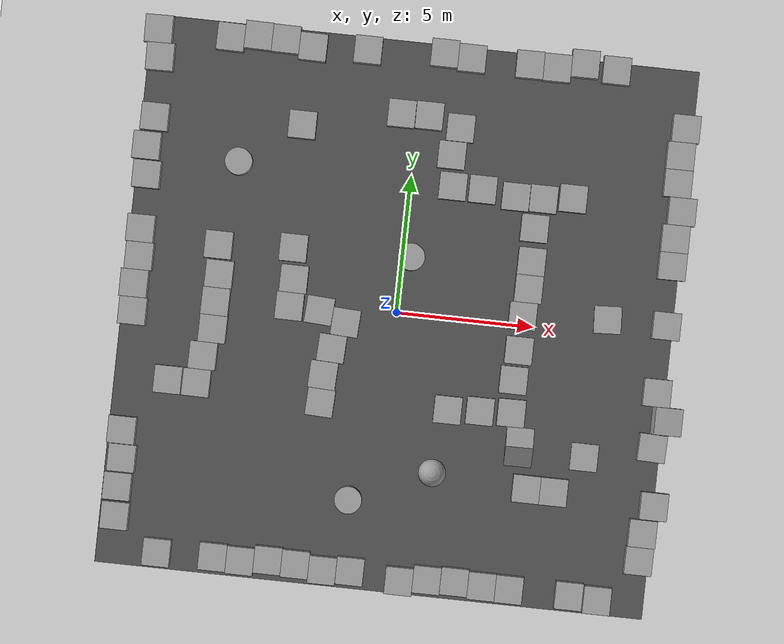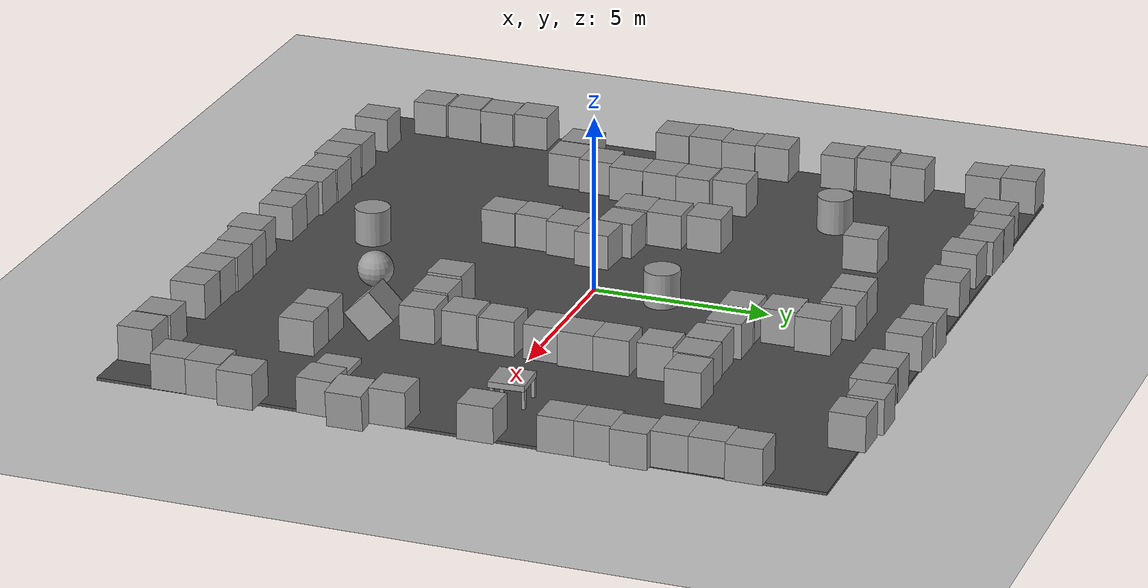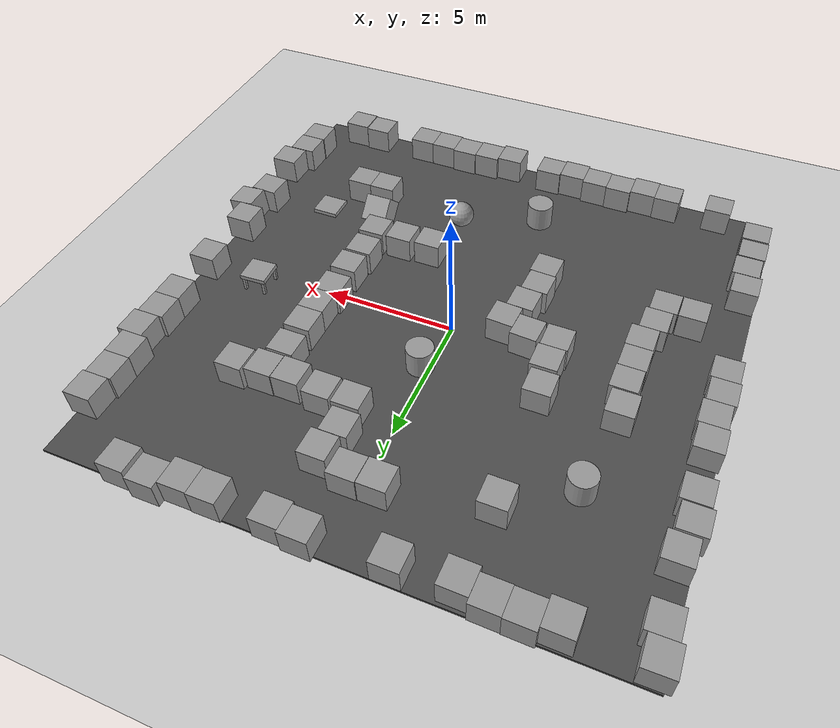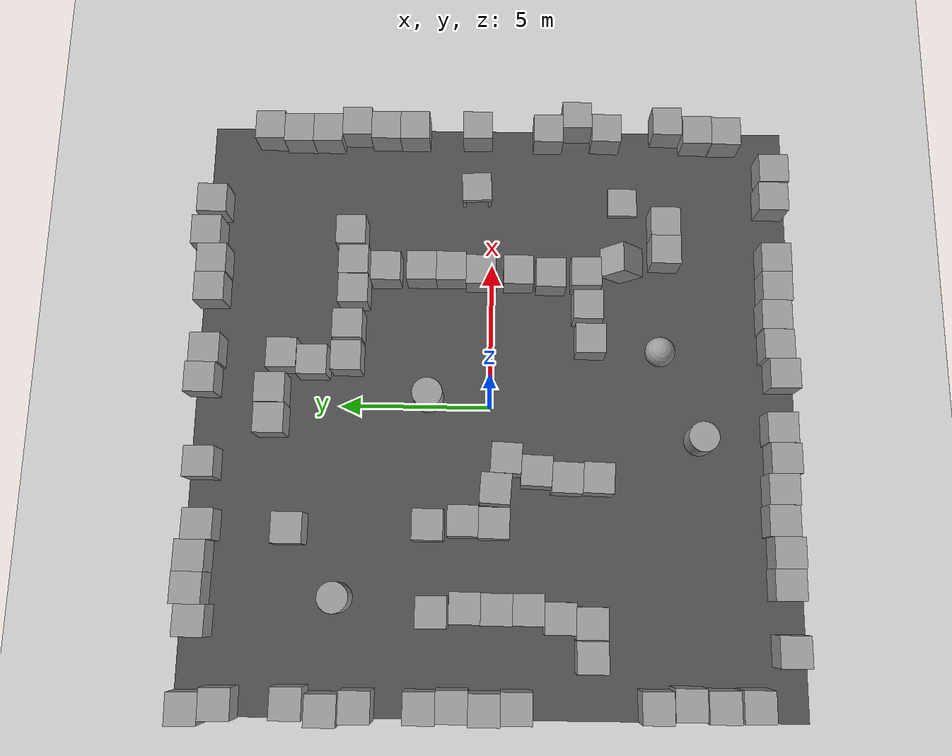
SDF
<sdf version="1.6">
 <world name="default">
  <light name="sun" type="directional">
   <pose>0 0 10 0 -0 0</pose>
   <diffuse>0.8 0.8 0.8 1</diffuse>
   <specular>0.1 0.1 0.1 1</specular>
   <attenuation>
    <range>1000</range>
    <constant>0.9</constant>
    <linear>0.01</linear>
    <quadratic>0.001</quadratic>
   </attenuation>
   <direction>-0.5 0.5 -1</direction>
  </light>
  <model name="ground_plane">
   <static>1</static>
   <link name="link">
    <collision name="collision">
     <geometry><plane><normal>0 0 1</normal><size>100 100</size></plane></geometry>
     <surface><friction><ode><mu>100</mu><mu2>50</mu2></ode></friction></surface>
    </collision>
    <visual name="visual">
     <cast_shadows>0</cast_shadows>
     <geometry><plane><normal>0 0 1</normal><size>100 100</size></plane></geometry>
     <material>
      <script><uri>file://media/materials/scripts/gazebo.material</uri><name>Gazebo/Grey</name></script>
     </material>
    </visual>
   </link>
  </model>
  <gravity>0 0 -9.8</gravity>
  <magnetic_field>6e-06 2.3e-05 -4.2e-05</magnetic_field>
  <atmosphere type="adiabatic"/>
  <physics name="default_physics" default="0" type="ode">
   <max_step_size>0.001</max_step_size>
   <real_time_factor>1</real_time_factor>
   <real_time_update_rate>1000</real_time_update_rate>
  </physics>
  <scene><ambient>0.4 0.4 0.4 1</ambient><background>0.7 0.7 0.7 1</background><shadows>1</shadows></scene>
  <spherical_coordinates>
   <surface_model>EARTH_WGS84</surface_model>
   <latitude_deg>0</latitude_deg>
   <longitude_deg>0</longitude_deg>
   <elevation>0</elevation>
   <heading_deg>0</heading_deg>
  </spherical_coordinates>
  <model name="asphalt_plane">
   <static>1</static>
   <link name="link">
    <collision name="collision"><geometry><box><size>20 20 0.1</size></box></geometry></collision>
    <visual name="visual">
     <cast_shadows>0</cast_shadows>
     <geometry><box><size>20 20 0.1</size></box></geometry>
     <material>
      <script>
       <uri>model://asphalt_plane/materials/scripts</uri>
       <uri>model://asphalt_plane/materials/textures</uri>
       <name>vrc/asphalt</name>
      </script>
     </material>
    </visual>
   </link>
   <pose>0.023839 -0.146036 0 0 -0 0</pose>
  </model>
  <model name="unit_box_0">
   <pose>-9.39334 -8.37793 0.549996 9e-06 0 2.1e-05</pose>
   <link name="link">
    <inertial>
     <mass>1</mass>
     <inertia>
      <ixx>0.166667</ixx>
      <ixy>0</ixy>
      <ixz>0</ixz>
      <iyy>0.166667</iyy>
      <iyz>0</iyz>
      <izz>0.166667</izz>
     </inertia>
    </inertial>
    <collision name="collision"><geometry><box><size>1 1 1</size></box></geometry></collision>
    <visual name="visual">
     <geometry><box><size>1 1 1</size></box></geometry>
     <material>
      <script><name>Gazebo/Grey</name><uri>file://media/materials/scripts/gazebo.material</uri></script>
     </material>
    </visual>
   </link>
  </model>
  <model name="unit_box_1">
   <pose>-9.41764 -7.31554 0.549996 9e-06 0 2.1e-05</pose>
   <link name="link">
    <inertial>
     <mass>1</mass>
     <inertia>
      <ixx>0.166667</ixx>
      <ixy>0</ixy>
      <ixz>0</ixz>
      <iyy>0.166667</iyy>
      <iyz>0</iyz>
      <izz>0.166667</izz>
     </inertia>
    </inertial>
    <collision name="collision"><geometry><box><size>1 1 1</size></box></geometry></collision>
    <visual name="visual">
     <geometry><box><size>1 1 1</size></box></geometry>
     <material>
      <script><name>Gazebo/Grey</name><uri>file://media/materials/scripts/gazebo.material</uri></script>
     </material>
    </visual>
   </link>
  </model>
  <model name="unit_box_1_clone">
   <pose>-9.36199 -6.27955 0.549996 9e-06 -0 7.6e-05</pose>
   <link name="link">
    <inertial>
     <mass>1</mass>
     <inertia>
      <ixx>0.166667</ixx>
      <ixy>0</ixy>
      <ixz>0</ixz>
      <iyy>0.166667</iyy>
      <iyz>0</iyz>
      <izz>0.166667</izz>
     </inertia>
    </inertial>
    <collision name="collision"><geometry><box><size>1 1 1</size></box></geometry></collision>
    <visual name="visual">
     <geometry><box><size>1 1 1</size></box></geometry>
     <material>
      <script><name>Gazebo/Grey</name><uri>file://media/materials/scripts/gazebo.material</uri></script>
     </material>
    </visual>
   </link>
  </model>
  <model name="unit_box_1_clone_0">
   <pose>-9.46654 -5.27001 0.549996 9e-06 0 7.5e-05</pose>
   <link name="link">
    <inertial>
     <mass>1</mass>
     <inertia>
      <ixx>0.166667</ixx>
      <ixy>0</ixy>
      <ixz>0</ixz>
      <iyy>0.166667</iyy>
      <iyz>0</iyz>
      <izz>0.166667</izz>
     </inertia>
    </inertial>
    <collision name="collision"><geometry><box><size>1 1 1</size></box></geometry></collision>
    <visual name="visual">
     <geometry><box><size>1 1 1</size></box></geometry>
     <material>
      <script><name>Gazebo/Grey</name><uri>file://media/materials/scripts/gazebo.material</uri></script>
     </material>
    </visual>
   </link>
  </model>
  <model name="unit_box_1_clone_1">
   <pose>-7.99794 -3.28029 0.549996 9e-06 -0 7.4e-05</pose>
   <link name="link">
    <inertial>
     <mass>1</mass>
     <inertia>
      <ixx>0.166667</ixx>
      <ixy>0</ixy>
      <ixz>0</ixz>
      <iyy>0.166667</iyy>
      <iyz>0</iyz>
      <izz>0.166667</izz>
     </inertia>
    </inertial>
    <collision name="collision"><geometry><box><size>1 1 1</size></box></geometry></collision>
    <visual name="visual">
     <geometry><box><size>1 1 1</size></box></geometry>
     <material>
      <script><name>Gazebo/Grey</name><uri>file://media/materials/scripts/gazebo.material</uri></script>
     </material>
    </visual>
   </link>
  </model>
  <model name="unit_box_1_clone_2">
   <pose>-6.96348 -3.28332 0.549996 9e-06 0 -0.008605</pose>
   <link name="link">
    <inertial>
     <mass>1</mass>
     <inertia>
      <ixx>0.166667</ixx>
      <ixy>0</ixy>
      <ixz>0</ixz>
      <iyy>0.166667</iyy>
      <iyz>0</iyz>
      <izz>0.166667</izz>
     </inertia>
    </inertial>
    <collision name="collision"><geometry><box><size>1 1 1</size></box></geometry></collision>
    <visual name="visual">
     <geometry><box><size>1 1 1</size></box></geometry>
     <material>
      <script><name>Gazebo/Grey</name><uri>file://media/materials/scripts/gazebo.material</uri></script>
     </material>
    </visual>
   </link>
  </model>
  <model name="unit_box_1_clone_3">
   <pose>-6.82914 -2.28436 0.549996 9e-06 0 -0.008661</pose>
   <link name="link">
    <inertial>
     <mass>1</mass>
     <inertia>
      <ixx>0.166667</ixx>
      <ixy>0</ixy>
      <ixz>0</ixz>
      <iyy>0.166667</iyy>
      <iyz>0</iyz>
      <izz>0.166667</izz>
     </inertia>
    </inertial>
    <collision name="collision"><geometry><box><size>1 1 1</size></box></geometry></collision>
    <visual name="visual">
     <geometry><box><size>1 1 1</size></box></geometry>
     <material>
      <script><name>Gazebo/Grey</name><uri>file://media/materials/scripts/gazebo.material</uri></script>
     </material>
    </visual>
   </link>
  </model>
  <model name="unit_box_1_clone_4">
   <pose>-6.57612 -1.28593 0.549996 9e-06 0 -0.007904</pose>
   <link name="link">
    <inertial>
     <mass>1</mass>
     <inertia>
      <ixx>0.166667</ixx>
      <ixy>0</ixy>
      <ixz>0</ixz>
      <iyy>0.166667</iyy>
      <iyz>0</iyz>
      <izz>0.166667</izz>
     </inertia>
    </inertial>
    <collision name="collision"><geometry><box><size>1 1 1</size></box></geometry></collision>
    <visual name="visual">
     <geometry><box><size>1 1 1</size></box></geometry>
     <material>
      <script><name>Gazebo/Grey</name><uri>file://media/materials/scripts/gazebo.material</uri></script>
     </material>
    </visual>
   </link>
  </model>
  <model name="unit_box_1_clone_5">
   <pose>-6.58122 -0.285844 0.549996 9e-06 0 -0.007904</pose>
   <link name="link">
    <inertial>
     <mass>1</mass>
     <inertia>
      <ixx>0.166667</ixx>
      <ixy>0</ixy>
      <ixz>0</ixz>
      <iyy>0.166667</iyy>
      <iyz>0</iyz>
      <izz>0.166667</izz>
     </inertia>
    </inertial>
    <collision name="collision"><geometry><box><size>1 1 1</size></box></geometry></collision>
    <visual name="visual">
     <geometry><box><size>1 1 1</size></box></geometry>
     <material>
      <script><name>Gazebo/Grey</name><uri>file://media/materials/scripts/gazebo.material</uri></script>
     </material>
    </visual>
   </link>
  </model>
  <model name="unit_box_1_clone_6">
   <pose>-6.55061 0.714163 0.549996 9e-06 -0 -0.008004</pose>
   <link name="link">
    <inertial>
     <mass>1</mass>
     <inertia>
      <ixx>0.166667</ixx>
      <ixy>0</ixy>
      <ixz>0</ixz>
      <iyy>0.166667</iyy>
      <iyz>0</iyz>
      <izz>0.166667</izz>
     </inertia>
    </inertial>
    <collision name="collision"><geometry><box><size>1 1 1</size></box></geometry></collision>
    <visual name="visual">
     <geometry><box><size>1 1 1</size></box></geometry>
     <material>
      <script><name>Gazebo/Grey</name><uri>file://media/materials/scripts/gazebo.material</uri></script>
     </material>
    </visual>
   </link>
  </model>
  <model name="unit_box_2">
   <pose>-6.68236 1.7653 0.549995 -1e-05 -0 2.1e-05</pose>
   <link name="link">
    <inertial>
     <mass>1</mass>
     <inertia>
      <ixx>0.166667</ixx>
      <ixy>0</ixy>
      <ixz>0</ixz>
      <iyy>0.166667</iyy>
      <iyz>0</iyz>
      <izz>0.166667</izz>
     </inertia>
    </inertial>
    <collision name="collision"><geometry><box><size>1 1 1</size></box></geometry></collision>
    <visual name="visual">
     <geometry><box><size>1 1 1</size></box></geometry>
     <material>
      <script><name>Gazebo/Grey</name><uri>file://media/materials/scripts/gazebo.material</uri></script>
     </material>
    </visual>
   </link>
  </model>
  <model name="unit_box_1_clone_7">
   <pose>-0.705026 -9.49284 0.549998 -1e-06 4e-06 -0.003058</pose>
   <link name="link">
    <inertial>
     <mass>1</mass>
     <inertia>
      <ixx>0.166667</ixx>
      <ixy>0</ixy>
      <ixz>0</ixz>
      <iyy>0.166667</iyy>
      <iyz>0</iyz>
      <izz>0.166667</izz>
     </inertia>
    </inertial>
    <collision name="collision"><geometry><box><size>1 1 1</size></box></geometry></collision>
    <visual name="visual">
     <geometry><box><size>1 1 1</size></box></geometry>
     <material>
      <script><name>Gazebo/Grey</name><uri>file://media/materials/scripts/gazebo.material</uri></script>
     </material>
    </visual>
   </link>
  </model>
  <model name="unit_box_1_clone_8">
   <pose>-1.70732 -9.56118 0.549998 -1e-06 4e-06 0.000224</pose>
   <link name="link">
    <inertial>
     <mass>1</mass>
     <inertia>
      <ixx>0.166667</ixx>
      <ixy>0</ixy>
      <ixz>0</ixz>
      <iyy>0.166667</iyy>
      <iyz>0</iyz>
      <izz>0.166667</izz>
     </inertia>
    </inertial>
    <collision name="collision"><geometry><box><size>1 1 1</size></box></geometry></collision>
    <visual name="visual">
     <geometry><box><size>1 1 1</size></box></geometry>
     <material>
      <script><name>Gazebo/Grey</name><uri>file://media/materials/scripts/gazebo.material</uri></script>
     </material>
    </visual>
   </link>
  </model>
  <model name="unit_box_1_clone_9">
   <pose>-2.70758 -9.44657 0.549995 -1e-05 -0 0.000276</pose>
   <link name="link">
    <inertial>
     <mass>1</mass>
     <inertia>
      <ixx>0.166667</ixx>
      <ixy>0</ixy>
      <ixz>0</ixz>
      <iyy>0.166667</iyy>
      <iyz>0</iyz>
      <izz>0.166667</izz>
     </inertia>
    </inertial>
    <collision name="collision"><geometry><box><size>1 1 1</size></box></geometry></collision>
    <visual name="visual">
     <geometry><box><size>1 1 1</size></box></geometry>
     <material>
      <script><name>Gazebo/Grey</name><uri>file://media/materials/scripts/gazebo.material</uri></script>
     </material>
    </visual>
   </link>
  </model>
  <model name="unit_box_1_clone_10">
   <pose>-3.70789 -9.40962 0.549996 9e-06 -0 0.000216</pose>
   <link name="link">
    <inertial>
     <mass>1</mass>
     <inertia>
      <ixx>0.166667</ixx>
      <ixy>0</ixy>
      <ixz>0</ixz>
      <iyy>0.166667</iyy>
      <iyz>0</iyz>
      <izz>0.166667</izz>
     </inertia>
    </inertial>
    <collision name="collision"><geometry><box><size>1 1 1</size></box></geometry></collision>
    <visual name="visual">
     <geometry><box><size>1 1 1</size></box></geometry>
     <material>
      <script><name>Gazebo/Grey</name><uri>file://media/materials/scripts/gazebo.material</uri></script>
     </material>
    </visual>
   </link>
  </model>
  <model name="unit_box_1_clone_11">
   <pose>-4.7079 -9.53282 0.549996 9e-06 -0 0.000276</pose>
   <link name="link">
    <inertial>
     <mass>1</mass>
     <inertia>
      <ixx>0.166667</ixx>
      <ixy>0</ixy>
      <ixz>0</ixz>
      <iyy>0.166667</iyy>
      <iyz>0</iyz>
      <izz>0.166667</izz>
     </inertia>
    </inertial>
    <collision name="collision"><geometry><box><size>1 1 1</size></box></geometry></collision>
    <visual name="visual">
     <geometry><box><size>1 1 1</size></box></geometry>
     <material>
      <script><name>Gazebo/Grey</name><uri>file://media/materials/scripts/gazebo.material</uri></script>
     </material>
    </visual>
   </link>
  </model>
  <model name="unit_box_1_clone_12">
   <pose>-5.70792 -9.49714 0.549996 9e-06 -0 0.000294</pose>
   <link name="link">
    <inertial>
     <mass>1</mass>
     <inertia>
      <ixx>0.166667</ixx>
      <ixy>0</ixy>
      <ixz>0</ixz>
      <iyy>0.166667</iyy>
      <iyz>0</iyz>
      <izz>0.166667</izz>
     </inertia>
    </inertial>
    <collision name="collision"><geometry><box><size>1 1 1</size></box></geometry></collision>
    <visual name="visual">
     <geometry><box><size>1 1 1</size></box></geometry>
     <material>
      <script><name>Gazebo/Grey</name><uri>file://media/materials/scripts/gazebo.material</uri></script>
     </material>
    </visual>
   </link>
  </model>
  <model name="unit_box_1_clone_13">
   <pose>-7.74684 -9.54883 0.549996 9e-06 -0 6.6e-05</pose>
   <link name="link">
    <inertial>
     <mass>1</mass>
     <inertia>
      <ixx>0.166667</ixx>
      <ixy>0</ixy>
      <ixz>0</ixz>
      <iyy>0.166667</iyy>
      <iyz>0</iyz>
      <izz>0.166667</izz>
     </inertia>
    </inertial>
    <collision name="collision"><geometry><box><size>1 1 1</size></box></geometry></collision>
    <visual name="visual">
     <geometry><box><size>1 1 1</size></box></geometry>
     <material>
      <script><name>Gazebo/Grey</name><uri>file://media/materials/scripts/gazebo.material</uri></script>
     </material>
    </visual>
   </link>
  </model>
  <model name="unit_box_1_clone_14">
   <pose>1.09207 -9.6549 0.55 0 -0 0.001285</pose>
   <link name="link">
    <inertial>
     <mass>1</mass>
     <inertia>
      <ixx>0.166667</ixx>
      <ixy>0</ixy>
      <ixz>0</ixz>
      <iyy>0.166667</iyy>
      <iyz>0</iyz>
      <izz>0.166667</izz>
     </inertia>
    </inertial>
    <collision name="collision"><geometry><box><size>1 1 1</size></box></geometry></collision>
    <visual name="visual">
     <geometry><box><size>1 1 1</size></box></geometry>
     <material>
      <script><name>Gazebo/Grey</name><uri>file://media/materials/scripts/gazebo.material</uri></script>
     </material>
    </visual>
   </link>
  </model>
  <model name="unit_box_1_clone_15">
   <pose>2.09212 -9.51207 0.549996 9e-06 -0 0.000929</pose>
   <link name="link">
    <inertial>
     <mass>1</mass>
     <inertia>
      <ixx>0.166667</ixx>
      <ixy>0</ixy>
      <ixz>0</ixz>
      <iyy>0.166667</iyy>
      <iyz>0</iyz>
      <izz>0.166667</izz>
     </inertia>
    </inertial>
    <collision name="collision"><geometry><box><size>1 1 1</size></box></geometry></collision>
    <visual name="visual">
     <geometry><box><size>1 1 1</size></box></geometry>
     <material>
      <script><name>Gazebo/Grey</name><uri>file://media/materials/scripts/gazebo.material</uri></script>
     </material>
    </visual>
   </link>
  </model>
  <model name="unit_box_1_clone_16">
   <pose>3.09306 -9.47292 0.549996 9e-06 -0 -0.000398</pose>
   <link name="link">
    <inertial>
     <mass>1</mass>
     <inertia>
      <ixx>0.166667</ixx>
      <ixy>0</ixy>
      <ixz>0</ixz>
      <iyy>0.166667</iyy>
      <iyz>0</iyz>
      <izz>0.166667</izz>
     </inertia>
    </inertial>
    <collision name="collision"><geometry><box><size>1 1 1</size></box></geometry></collision>
    <visual name="visual">
     <geometry><box><size>1 1 1</size></box></geometry>
     <material>
      <script><name>Gazebo/Grey</name><uri>file://media/materials/scripts/gazebo.material</uri></script>
     </material>
    </visual>
   </link>
  </model>
  <model name="unit_box_1_clone_17">
   <pose>4.09327 -9.53323 0.549996 9e-06 -0 -0.000767</pose>
   <link name="link">
    <inertial>
     <mass>1</mass>
     <inertia>
      <ixx>0.166667</ixx>
      <ixy>0</ixy>
      <ixz>0</ixz>
      <iyy>0.166667</iyy>
      <iyz>0</iyz>
      <izz>0.166667</izz>
     </inertia>
    </inertial>
    <collision name="collision"><geometry><box><size>1 1 1</size></box></geometry></collision>
    <visual name="visual">
     <geometry><box><size>1 1 1</size></box></geometry>
     <material>
      <script><name>Gazebo/Grey</name><uri>file://media/materials/scripts/gazebo.material</uri></script>
     </material>
    </visual>
   </link>
  </model>
  <model name="unit_box_1_clone_18">
   <pose>5.09332 -9.54521 0.549996 9e-06 -0 -0.000875</pose>
   <link name="link">
    <inertial>
     <mass>1</mass>
     <inertia>
      <ixx>0.166667</ixx>
      <ixy>0</ixy>
      <ixz>0</ixz>
      <iyy>0.166667</iyy>
      <iyz>0</iyz>
      <izz>0.166667</izz>
     </inertia>
    </inertial>
    <collision name="collision"><geometry><box><size>1 1 1</size></box></geometry></collision>
    <visual name="visual">
     <geometry><box><size>1 1 1</size></box></geometry>
     <material>
      <script><name>Gazebo/Grey</name><uri>file://media/materials/scripts/gazebo.material</uri></script>
     </material>
    </visual>
   </link>
  </model>
  <model name="unit_box_1_clone_19">
   <pose>7.27243 -9.54386 0.549996 9e-06 -0 6.2e-05</pose>
   <link name="link">
    <inertial>
     <mass>1</mass>
     <inertia>
      <ixx>0.166667</ixx>
      <ixy>0</ixy>
      <ixz>0</ixz>
      <iyy>0.166667</iyy>
      <iyz>0</iyz>
      <izz>0.166667</izz>
     </inertia>
    </inertial>
    <collision name="collision"><geometry><box><size>1 1 1</size></box></geometry></collision>
    <visual name="visual">
     <geometry><box><size>1 1 1</size></box></geometry>
     <material>
      <script><name>Gazebo/Grey</name><uri>file://media/materials/scripts/gazebo.material</uri></script>
     </material>
    </visual>
   </link>
  </model>
  <model name="unit_box_1_clone_20">
   <pose>8.30474 -9.59831 0.549996 9e-06 -0 6.2e-05</pose>
   <link name="link">
    <inertial>
     <mass>1</mass>
     <inertia>
      <ixx>0.166667</ixx>
      <ixy>0</ixy>
      <ixz>0</ixz>
      <iyy>0.166667</iyy>
      <iyz>0</iyz>
      <izz>0.166667</izz>
     </inertia>
    </inertial>
    <collision name="collision"><geometry><box><size>1 1 1</size></box></geometry></collision>
    <visual name="visual">
     <geometry><box><size>1 1 1</size></box></geometry>
     <material>
      <script><name>Gazebo/Grey</name><uri>file://media/materials/scripts/gazebo.material</uri></script>
     </material>
    </visual>
   </link>
  </model>
  <model name="unit_box_1_clone_21">
   <pose>9.65896 -8.02131 0.55 0 0 -0.004066</pose>
   <link name="link">
    <inertial>
     <mass>1</mass>
     <inertia>
      <ixx>0.166667</ixx>
      <ixy>0</ixy>
      <ixz>0</ixz>
      <iyy>0.166667</iyy>
      <iyz>0</iyz>
      <izz>0.166667</izz>
     </inertia>
    </inertial>
    <collision name="collision"><geometry><box><size>1 1 1</size></box></geometry></collision>
    <visual name="visual">
     <geometry><box><size>1 1 1</size></box></geometry>
     <material>
      <script><name>Gazebo/Grey</name><uri>file://media/materials/scripts/gazebo.material</uri></script>
     </material>
    </visual>
   </link>
  </model>
  <model name="unit_box_1_clone_22">
   <pose>9.69096 -7.0214 0.549996 0 9e-06 -0.004069</pose>
   <link name="link">
    <inertial>
     <mass>1</mass>
     <inertia>
      <ixx>0.166667</ixx>
      <ixy>0</ixy>
      <ixz>0</ixz>
      <iyy>0.166667</iyy>
      <iyz>0</iyz>
      <izz>0.166667</izz>
     </inertia>
    </inertial>
    <collision name="collision"><geometry><box><size>1 1 1</size></box></geometry></collision>
    <visual name="visual">
     <geometry><box><size>1 1 1</size></box></geometry>
     <material>
      <script><name>Gazebo/Grey</name><uri>file://media/materials/scripts/gazebo.material</uri></script>
     </material>
    </visual>
   </link>
  </model>
  <model name="unit_box_1_clone_23">
   <pose>10 -6 0.549999 2e-06 -0 -1.1e-05</pose>
   <link name="link">
    <inertial>
     <mass>1</mass>
     <inertia>
      <ixx>0.166667</ixx>
      <ixy>0</ixy>
      <ixz>0</ixz>
      <iyy>0.166667</iyy>
      <iyz>0</iyz>
      <izz>0.166667</izz>
     </inertia>
    </inertial>
    <collision name="collision"><geometry><box><size>1 1 1</size></box></geometry></collision>
    <visual name="visual">
     <geometry><box><size>1 1 1</size></box></geometry>
     <material>
      <script><name>Gazebo/Grey</name><uri>file://media/materials/scripts/gazebo.material</uri></script>
     </material>
    </visual>
   </link>
  </model>
  <model name="unit_box_1_clone_24">
   <pose>9.71569 -3.89853 0.55 0 0 -0.031692</pose>
   <link name="link">
    <inertial>
     <mass>1</mass>
     <inertia>
      <ixx>0.166667</ixx>
      <ixy>0</ixy>
      <ixz>0</ixz>
      <iyy>0.166667</iyy>
      <iyz>0</iyz>
      <izz>0.166667</izz>
     </inertia>
    </inertial>
    <collision name="collision"><geometry><box><size>1 1 1</size></box></geometry></collision>
    <visual name="visual">
     <geometry><box><size>1 1 1</size></box></geometry>
     <material>
      <script><name>Gazebo/Grey</name><uri>file://media/materials/scripts/gazebo.material</uri></script>
     </material>
    </visual>
   </link>
  </model>
  <model name="unit_box_1_clone_25">
   <pose>10.1525 -2.89312 0.540837 0.000252 0.085144 0.002965</pose>
   <link name="link">
    <inertial>
     <mass>1</mass>
     <inertia>
      <ixx>0.166667</ixx>
      <ixy>0</ixy>
      <ixz>0</ixz>
      <iyy>0.166667</iyy>
      <iyz>0</iyz>
      <izz>0.166667</izz>
     </inertia>
    </inertial>
    <collision name="collision"><geometry><box><size>1 1 1</size></box></geometry></collision>
    <visual name="visual">
     <geometry><box><size>1 1 1</size></box></geometry>
     <material>
      <script><name>Gazebo/Grey</name><uri>file://media/materials/scripts/gazebo.material</uri></script>
     </material>
    </visual>
   </link>
  </model>
  <model name="unit_box_1_clone_26">
   <pose>9.68456 -1.89437 0.549999 -2e-06 3e-06 0.002944</pose>
   <link name="link">
    <inertial>
     <mass>1</mass>
     <inertia>
      <ixx>0.166667</ixx>
      <ixy>0</ixy>
      <ixz>0</ixz>
      <iyy>0.166667</iyy>
      <iyz>0</iyz>
      <izz>0.166667</izz>
     </inertia>
    </inertial>
    <collision name="collision"><geometry><box><size>1 1 1</size></box></geometry></collision>
    <visual name="visual">
     <geometry><box><size>1 1 1</size></box></geometry>
     <material>
      <script><name>Gazebo/Grey</name><uri>file://media/materials/scripts/gazebo.material</uri></script>
     </material>
    </visual>
   </link>
  </model>
  <model name="unit_box_1_clone_27">
   <pose>9.76856 0.548242 0.55 0 -0 3.5e-05</pose>
   <link name="link">
    <inertial>
     <mass>1</mass>
     <inertia>
      <ixx>0.166667</ixx>
      <ixy>0</ixy>
      <ixz>0</ixz>
      <iyy>0.166667</iyy>
      <iyz>0</iyz>
      <izz>0.166667</izz>
     </inertia>
    </inertial>
    <collision name="collision"><geometry><box><size>1 1 1</size></box></geometry></collision>
    <visual name="visual">
     <geometry><box><size>1 1 1</size></box></geometry>
     <material>
      <script><name>Gazebo/Grey</name><uri>file://media/materials/scripts/gazebo.material</uri></script>
     </material>
    </visual>
   </link>
  </model>
  <model name="unit_box_1_clone_28">
   <pose>9.74804 2.72075 0.549994 -4e-06 8e-06 0.004111</pose>
   <link name="link">
    <inertial>
     <mass>1</mass>
     <inertia>
      <ixx>0.166667</ixx>
      <ixy>0</ixy>
      <ixz>0</ixz>
      <iyy>0.166667</iyy>
      <iyz>0</iyz>
      <izz>0.166667</izz>
     </inertia>
    </inertial>
    <collision name="collision"><geometry><box><size>1 1 1</size></box></geometry></collision>
    <visual name="visual">
     <geometry><box><size>1 1 1</size></box></geometry>
     <material>
      <script><name>Gazebo/Grey</name><uri>file://media/materials/scripts/gazebo.material</uri></script>
     </material>
    </visual>
   </link>
  </model>
  <model name="unit_box_1_clone_29">
   <pose>9.74822 3.72077 0.549994 -4e-06 8e-06 0.004107</pose>
   <link name="link">
    <inertial>
     <mass>1</mass>
     <inertia>
      <ixx>0.166667</ixx>
      <ixy>0</ixy>
      <ixz>0</ixz>
      <iyy>0.166667</iyy>
      <iyz>0</iyz>
      <izz>0.166667</izz>
     </inertia>
    </inertial>
    <collision name="collision"><geometry><box><size>1 1 1</size></box></geometry></collision>
    <visual name="visual">
     <geometry><box><size>1 1 1</size></box></geometry>
     <material>
      <script><name>Gazebo/Grey</name><uri>file://media/materials/scripts/gazebo.material</uri></script>
     </material>
    </visual>
   </link>
  </model>
  <model name="unit_box_1_clone_30">
   <pose>9.88777 4.72138 0.549997 5e-06 -1e-06 0.004127</pose>
   <link name="link">
    <inertial>
     <mass>1</mass>
     <inertia>
      <ixx>0.166667</ixx>
      <ixy>0</ixy>
      <ixz>0</ixz>
      <iyy>0.166667</iyy>
      <iyz>0</iyz>
      <izz>0.166667</izz>
     </inertia>
    </inertial>
    <collision name="collision"><geometry><box><size>1 1 1</size></box></geometry></collision>
    <visual name="visual">
     <geometry><box><size>1 1 1</size></box></geometry>
     <material>
      <script><name>Gazebo/Grey</name><uri>file://media/materials/scripts/gazebo.material</uri></script>
     </material>
    </visual>
   </link>
  </model>
  <model name="unit_box_1_clone_31">
   <pose>9.63354 5.72049 0.55 0 -0 0.004242</pose>
   <link name="link">
    <inertial>
     <mass>1</mass>
     <inertia>
      <ixx>0.166667</ixx>
      <ixy>0</ixy>
      <ixz>0</ixz>
      <iyy>0.166667</iyy>
      <iyz>0</iyz>
      <izz>0.166667</izz>
     </inertia>
    </inertial>
    <collision name="collision"><geometry><box><size>1 1 1</size></box></geometry></collision>
    <visual name="visual">
     <geometry><box><size>1 1 1</size></box></geometry>
     <material>
      <script><name>Gazebo/Grey</name><uri>file://media/materials/scripts/gazebo.material</uri></script>
     </material>
    </visual>
   </link>
  </model>
  <model name="unit_box_1_clone_32">
   <pose>9.62456 6.72048 0.549996 0 -9e-06 0.004241</pose>
   <link name="link">
    <inertial>
     <mass>1</mass>
     <inertia>
      <ixx>0.166667</ixx>
      <ixy>0</ixy>
      <ixz>0</ixz>
      <iyy>0.166667</iyy>
      <iyz>0</iyz>
      <izz>0.166667</izz>
     </inertia>
    </inertial>
    <collision name="collision"><geometry><box><size>1 1 1</size></box></geometry></collision>
    <visual name="visual">
     <geometry><box><size>1 1 1</size></box></geometry>
     <material>
      <script><name>Gazebo/Grey</name><uri>file://media/materials/scripts/gazebo.material</uri></script>
     </material>
    </visual>
   </link>
  </model>
  <model name="unit_box_1_clone_33">
   <pose>9.71779 7.72092 0.549996 0 8e-06 0.004295</pose>
   <link name="link">
    <inertial>
     <mass>1</mass>
     <inertia>
      <ixx>0.166667</ixx>
      <ixy>0</ixy>
      <ixz>0</ixz>
      <iyy>0.166667</iyy>
      <iyz>0</iyz>
      <izz>0.166667</izz>
     </inertia>
    </inertial>
    <collision name="collision"><geometry><box><size>1 1 1</size></box></geometry></collision>
    <visual name="visual">
     <geometry><box><size>1 1 1</size></box></geometry>
     <material>
      <script><name>Gazebo/Grey</name><uri>file://media/materials/scripts/gazebo.material</uri></script>
     </material>
    </visual>
   </link>
  </model>
  <model name="unit_box_1_clone_34">
   <pose>6.9999 9.55273 0.549999 0 2e-06 0.000429</pose>
   <link name="link">
    <inertial>
     <mass>1</mass>
     <inertia>
      <ixx>0.166667</ixx>
      <ixy>0</ixy>
      <ixz>0</ixz>
      <iyy>0.166667</iyy>
      <iyz>0</iyz>
      <izz>0.166667</izz>
     </inertia>
    </inertial>
    <collision name="collision"><geometry><box><size>1 1 1</size></box></geometry></collision>
    <visual name="visual">
     <geometry><box><size>1 1 1</size></box></geometry>
     <material>
      <script><name>Gazebo/Grey</name><uri>file://media/materials/scripts/gazebo.material</uri></script>
     </material>
    </visual>
   </link>
  </model>
  <model name="unit_box_1_clone_35">
   <pose>5.84877 9.67114 0.549996 3e-06 7e-06 0.011102</pose>
   <link name="link">
    <inertial>
     <mass>1</mass>
     <inertia>
      <ixx>0.166667</ixx>
      <ixy>0</ixy>
      <ixz>0</ixz>
      <iyy>0.166667</iyy>
      <iyz>0</iyz>
      <izz>0.166667</izz>
     </inertia>
    </inertial>
    <collision name="collision"><geometry><box><size>1 1 1</size></box></geometry></collision>
    <visual name="visual">
     <geometry><box><size>1 1 1</size></box></geometry>
     <material>
      <script><name>Gazebo/Grey</name><uri>file://media/materials/scripts/gazebo.material</uri></script>
     </material>
    </visual>
   </link>
  </model>
  <model name="unit_box_1_clone_36">
   <pose>4.85147 9.42217 0.55 0 -0 0.011103</pose>
   <link name="link">
    <inertial>
     <mass>1</mass>
     <inertia>
      <ixx>0.166667</ixx>
      <ixy>0</ixy>
      <ixz>0</ixz>
      <iyy>0.166667</iyy>
      <iyz>0</iyz>
      <izz>0.166667</izz>
     </inertia>
    </inertial>
    <collision name="collision"><geometry><box><size>1 1 1</size></box></geometry></collision>
    <visual name="visual">
     <geometry><box><size>1 1 1</size></box></geometry>
     <material>
      <script><name>Gazebo/Grey</name><uri>file://media/materials/scripts/gazebo.material</uri></script>
     </material>
    </visual>
   </link>
  </model>
  <model name="unit_box_1_clone_37">
   <pose>3.85126 9.43365 0.549988 1e-06 6e-06 0.011059</pose>
   <link name="link">
    <inertial>
     <mass>1</mass>
     <inertia>
      <ixx>0.166667</ixx>
      <ixy>0</ixy>
      <ixz>0</ixz>
      <iyy>0.166667</iyy>
      <iyz>0</iyz>
      <izz>0.166667</izz>
     </inertia>
    </inertial>
    <collision name="collision"><geometry><box><size>1 1 1</size></box></geometry></collision>
    <visual name="visual">
     <geometry><box><size>1 1 1</size></box></geometry>
     <material>
      <script><name>Gazebo/Grey</name><uri>file://media/materials/scripts/gazebo.material</uri></script>
     </material>
    </visual>
   </link>
  </model>
  <model name="unit_box_1_clone_38">
   <pose>1.74504 9.44139 0.549997 -7e-06 2e-06 -0.000691</pose>
   <link name="link">
    <inertial>
     <mass>1</mass>
     <inertia>
      <ixx>0.166667</ixx>
      <ixy>0</ixy>
      <ixz>0</ixz>
      <iyy>0.166667</iyy>
      <iyz>0</iyz>
      <izz>0.166667</izz>
     </inertia>
    </inertial>
    <collision name="collision"><geometry><box><size>1 1 1</size></box></geometry></collision>
    <visual name="visual">
     <geometry><box><size>1 1 1</size></box></geometry>
     <material>
      <script><name>Gazebo/Grey</name><uri>file://media/materials/scripts/gazebo.material</uri></script>
     </material>
    </visual>
   </link>
  </model>
  <model name="unit_box_1_clone_39">
   <pose>0.745098 9.52547 0.549998 -3e-06 -6e-06 -0.000691</pose>
   <link name="link">
    <inertial>
     <mass>1</mass>
     <inertia>
      <ixx>0.166667</ixx>
      <ixy>0</ixy>
      <ixz>0</ixz>
      <iyy>0.166667</iyy>
      <iyz>0</iyz>
      <izz>0.166667</izz>
     </inertia>
    </inertial>
    <collision name="collision"><geometry><box><size>1 1 1</size></box></geometry></collision>
    <visual name="visual">
     <geometry><box><size>1 1 1</size></box></geometry>
     <material>
      <script><name>Gazebo/Grey</name><uri>file://media/materials/scripts/gazebo.material</uri></script>
     </material>
    </visual>
   </link>
  </model>
  <model name="unit_box_1_clone_40">
   <pose>-2.0363 9.35144 0.549996 9e-06 -0 6.2e-05</pose>
   <link name="link">
    <inertial>
     <mass>1</mass>
     <inertia>
      <ixx>0.166667</ixx>
      <ixy>0</ixy>
      <ixz>0</ixz>
      <iyy>0.166667</iyy>
      <iyz>0</iyz>
      <izz>0.166667</izz>
     </inertia>
    </inertial>
    <collision name="collision"><geometry><box><size>1 1 1</size></box></geometry></collision>
    <visual name="visual">
     <geometry><box><size>1 1 1</size></box></geometry>
     <material>
      <script><name>Gazebo/Grey</name><uri>file://media/materials/scripts/gazebo.material</uri></script>
     </material>
    </visual>
   </link>
  </model>
  <model name="unit_box_1_clone_41">
   <pose>-4.02686 9.2434 0.549995 -0 1e-05 -0.009787</pose>
   <link name="link">
    <inertial>
     <mass>1</mass>
     <inertia>
      <ixx>0.166667</ixx>
      <ixy>0</ixy>
      <ixz>0</ixz>
      <iyy>0.166667</iyy>
      <iyz>0</iyz>
      <izz>0.166667</izz>
     </inertia>
    </inertial>
    <collision name="collision"><geometry><box><size>1 1 1</size></box></geometry></collision>
    <visual name="visual">
     <geometry><box><size>1 1 1</size></box></geometry>
     <material>
      <script><name>Gazebo/Grey</name><uri>file://media/materials/scripts/gazebo.material</uri></script>
     </material>
    </visual>
   </link>
  </model>
  <model name="unit_box_1_clone_42">
   <pose>-5.02535 9.42291 0.55 0 0 -0.00982</pose>
   <link name="link">
    <inertial>
     <mass>1</mass>
     <inertia>
      <ixx>0.166667</ixx>
      <ixy>0</ixy>
      <ixz>0</ixz>
      <iyy>0.166667</iyy>
      <iyz>0</iyz>
      <izz>0.166667</izz>
     </inertia>
    </inertial>
    <collision name="collision"><geometry><box><size>1 1 1</size></box></geometry></collision>
    <visual name="visual">
     <geometry><box><size>1 1 1</size></box></geometry>
     <material>
      <script><name>Gazebo/Grey</name><uri>file://media/materials/scripts/gazebo.material</uri></script>
     </material>
    </visual>
   </link>
  </model>
  <model name="unit_box_1_clone_43">
   <pose>-6.02527 9.44736 0.549996 -8e-06 -0 -0.009945</pose>
   <link name="link">
    <inertial>
     <mass>1</mass>
     <inertia>
      <ixx>0.166667</ixx>
      <ixy>0</ixy>
      <ixz>0</ixz>
      <iyy>0.166667</iyy>
      <iyz>0</iyz>
      <izz>0.166667</izz>
     </inertia>
    </inertial>
    <collision name="collision"><geometry><box><size>1 1 1</size></box></geometry></collision>
    <visual name="visual">
     <geometry><box><size>1 1 1</size></box></geometry>
     <material>
      <script><name>Gazebo/Grey</name><uri>file://media/materials/scripts/gazebo.material</uri></script>
     </material>
    </visual>
   </link>
  </model>
  <model name="unit_box_1_clone_44">
   <pose>-7.02697 9.29033 0.549998 -4e-06 -1e-06 -0.010038</pose>
   <link name="link">
    <inertial>
     <mass>1</mass>
     <inertia>
      <ixx>0.166667</ixx>
      <ixy>0</ixy>
      <ixz>0</ixz>
      <iyy>0.166667</iyy>
      <iyz>0</iyz>
      <izz>0.166667</izz>
     </inertia>
    </inertial>
    <collision name="collision"><geometry><box><size>1 1 1</size></box></geometry></collision>
    <visual name="visual">
     <geometry><box><size>1 1 1</size></box></geometry>
     <material>
      <script><name>Gazebo/Grey</name><uri>file://media/materials/scripts/gazebo.material</uri></script>
     </material>
    </visual>
   </link>
  </model>
  <model name="unit_box_1_clone_45">
   <pose>-9.65357 9.30938 0.55 0 -0 0.016627</pose>
   <link name="link">
    <inertial>
     <mass>1</mass>
     <inertia>
      <ixx>0.166667</ixx>
      <ixy>0</ixy>
      <ixz>0</ixz>
      <iyy>0.166667</iyy>
      <iyz>0</iyz>
      <izz>0.166667</izz>
     </inertia>
    </inertial>
    <collision name="collision"><geometry><box><size>1 1 1</size></box></geometry></collision>
    <visual name="visual">
     <geometry><box><size>1 1 1</size></box></geometry>
     <material>
      <script><name>Gazebo/Grey</name><uri>file://media/materials/scripts/gazebo.material</uri></script>
     </material>
    </visual>
   </link>
  </model>
  <model name="unit_box_1_clone_46">
   <pose>-9.50816 8.31159 0.55 0 -0 0.016775</pose>
   <link name="link">
    <inertial>
     <mass>1</mass>
     <inertia>
      <ixx>0.166667</ixx>
      <ixy>0</ixy>
      <ixz>0</ixz>
      <iyy>0.166667</iyy>
      <iyz>0</iyz>
      <izz>0.166667</izz>
     </inertia>
    </inertial>
    <collision name="collision"><geometry><box><size>1 1 1</size></box></geometry></collision>
    <visual name="visual">
     <geometry><box><size>1 1 1</size></box></geometry>
     <material>
      <script><name>Gazebo/Grey</name><uri>file://media/materials/scripts/gazebo.material</uri></script>
     </material>
    </visual>
   </link>
  </model>
  <model name="unit_box_1_clone_47">
   <pose>-9.46721 6.13597 0.55 0 -0 3.8e-05</pose>
   <link name="link">
    <inertial>
     <mass>1</mass>
     <inertia>
      <ixx>0.166667</ixx>
      <ixy>0</ixy>
      <ixz>0</ixz>
      <iyy>0.166667</iyy>
      <iyz>0</iyz>
      <izz>0.166667</izz>
     </inertia>
    </inertial>
    <collision name="collision"><geometry><box><size>1 1 1</size></box></geometry></collision>
    <visual name="visual">
     <geometry><box><size>1 1 1</size></box></geometry>
     <material>
      <script><name>Gazebo/Grey</name><uri>file://media/materials/scripts/gazebo.material</uri></script>
     </material>
    </visual>
   </link>
  </model>
  <model name="unit_box_1_clone_48">
   <pose>-9.65559 5.07226 0.550001 -0 -2e-06 3.3e-05</pose>
   <link name="link">
    <inertial>
     <mass>1</mass>
     <inertia>
      <ixx>0.166667</ixx>
      <ixy>0</ixy>
      <ixz>0</ixz>
      <iyy>0.166667</iyy>
      <iyz>0</iyz>
      <izz>0.166667</izz>
     </inertia>
    </inertial>
    <collision name="collision"><geometry><box><size>1 1 1</size></box></geometry></collision>
    <visual name="visual">
     <geometry><box><size>1 1 1</size></box></geometry>
     <material>
      <script><name>Gazebo/Grey</name><uri>file://media/materials/scripts/gazebo.material</uri></script>
     </material>
    </visual>
   </link>
  </model>
  <model name="unit_box_1_clone_49">
   <pose>-9.55136 4.03454 0.55 0 -0 7.4e-05</pose>
   <link name="link">
    <inertial>
     <mass>1</mass>
     <inertia>
      <ixx>0.166667</ixx>
      <ixy>0</ixy>
      <ixz>0</ixz>
      <iyy>0.166667</iyy>
      <iyz>0</iyz>
      <izz>0.166667</izz>
     </inertia>
    </inertial>
    <collision name="collision"><geometry><box><size>1 1 1</size></box></geometry></collision>
    <visual name="visual">
     <geometry><box><size>1 1 1</size></box></geometry>
     <material>
      <script><name>Gazebo/Grey</name><uri>file://media/materials/scripts/gazebo.material</uri></script>
     </material>
    </visual>
   </link>
  </model>
  <model name="unit_box_1_clone_50">
   <pose>-9.55709 2.06439 0.55 -3e-06 -3e-06 0.00222</pose>
   <link name="link">
    <inertial>
     <mass>1</mass>
     <inertia>
      <ixx>0.166667</ixx>
      <ixy>0</ixy>
      <ixz>0</ixz>
      <iyy>0.166667</iyy>
      <iyz>0</iyz>
      <izz>0.166667</izz>
     </inertia>
    </inertial>
    <collision name="collision"><geometry><box><size>1 1 1</size></box></geometry></collision>
    <visual name="visual">
     <geometry><box><size>1 1 1</size></box></geometry>
     <material>
      <script><name>Gazebo/Grey</name><uri>file://media/materials/scripts/gazebo.material</uri></script>
     </material>
    </visual>
   </link>
  </model>
  <model name="unit_box_1_clone_51">
   <pose>-9.50404 1.06442 0.549995 -0 1e-05 0.002374</pose>
   <link name="link">
    <inertial>
     <mass>1</mass>
     <inertia>
      <ixx>0.166667</ixx>
      <ixy>0</ixy>
      <ixz>0</ixz>
      <iyy>0.166667</iyy>
      <iyz>0</iyz>
      <izz>0.166667</izz>
     </inertia>
    </inertial>
    <collision name="collision"><geometry><box><size>1 1 1</size></box></geometry></collision>
    <visual name="visual">
     <geometry><box><size>1 1 1</size></box></geometry>
     <material>
      <script><name>Gazebo/Grey</name><uri>file://media/materials/scripts/gazebo.material</uri></script>
     </material>
    </visual>
   </link>
  </model>
  <model name="unit_box_1_clone_52">
   <pose>-9.58873 0.06415 0.549998 4e-06 1e-06 0.002487</pose>
   <link name="link">
    <inertial>
     <mass>1</mass>
     <inertia>
      <ixx>0.166667</ixx>
      <ixy>0</ixy>
      <ixz>0</ixz>
      <iyy>0.166667</iyy>
      <iyz>0</iyz>
      <izz>0.166667</izz>
     </inertia>
    </inertial>
    <collision name="collision"><geometry><box><size>1 1 1</size></box></geometry></collision>
    <visual name="visual">
     <geometry><box><size>1 1 1</size></box></geometry>
     <material>
      <script><name>Gazebo/Grey</name><uri>file://media/materials/scripts/gazebo.material</uri></script>
     </material>
    </visual>
   </link>
  </model>
  <model name="unit_box_1_clone_53">
   <pose>-9.53464 -0.935743 0.55 0 -0 0.002478</pose>
   <link name="link">
    <inertial>
     <mass>1</mass>
     <inertia>
      <ixx>0.166667</ixx>
      <ixy>0</ixy>
      <ixz>0</ixz>
      <iyy>0.166667</iyy>
      <iyz>0</iyz>
      <izz>0.166667</izz>
     </inertia>
    </inertial>
    <collision name="collision"><geometry><box><size>1 1 1</size></box></geometry></collision>
    <visual name="visual">
     <geometry><box><size>1 1 1</size></box></geometry>
     <material>
      <script><name>Gazebo/Grey</name><uri>file://media/materials/scripts/gazebo.material</uri></script>
     </material>
    </visual>
   </link>
  </model>
  <model name="unit_box_1_clone_54">
   <pose>-4.11779 6.4088 0.55 0 -0 3.8e-05</pose>
   <link name="link">
    <inertial>
     <mass>1</mass>
     <inertia>
      <ixx>0.166667</ixx>
      <ixy>0</ixy>
      <ixz>0</ixz>
      <iyy>0.166667</iyy>
      <iyz>0</iyz>
      <izz>0.166667</izz>
     </inertia>
    </inertial>
    <collision name="collision"><geometry><box><size>1 1 1</size></box></geometry></collision>
    <visual name="visual">
     <geometry><box><size>1 1 1</size></box></geometry>
     <material>
      <script><name>Gazebo/Grey</name><uri>file://media/materials/scripts/gazebo.material</uri></script>
     </material>
    </visual>
   </link>
  </model>
  <model name="unit_sphere_0">
   <pose>1.87814 -5.638 0.55 0 -0 0</pose>
   <link name="link">
    <inertial>
     <mass>1</mass>
     <inertia><ixx>0.1</ixx><ixy>0</ixy><ixz>0</ixz><iyy>0.1</iyy><iyz>0</iyz><izz>0.1</izz></inertia>
    </inertial>
    <collision name="collision"><geometry><sphere><radius>0.5</radius></sphere></geometry></collision>
    <visual name="visual">
     <geometry><sphere><radius>0.5</radius></sphere></geometry>
     <material>
      <script><name>Gazebo/Grey</name><uri>file://media/materials/scripts/gazebo.material</uri></script>
     </material>
    </visual>
   </link>
  </model>
  <model name="unit_box_3">
   <pose>-2.41862 -3.52642 0.549997 0 -7e-06 -0.04261</pose>
   <link name="link">
    <inertial>
     <mass>1</mass>
     <inertia>
      <ixx>0.166667</ixx>
      <ixy>0</ixy>
      <ixz>0</ixz>
      <iyy>0.166667</iyy>
      <iyz>0</iyz>
      <izz>0.166667</izz>
     </inertia>
    </inertial>
    <collision name="collision"><geometry><box><size>1 1 1</size></box></geometry></collision>
    <visual name="visual">
     <geometry><box><size>1 1 1</size></box></geometry>
     <material>
      <script><name>Gazebo/Grey</name><uri>file://media/materials/scripts/gazebo.material</uri></script>
     </material>
    </visual>
   </link>
  </model>
  <model name="unit_box_1_clone_55">
   <pose>-2.42251 -2.52504 0.55 0 0 -0.042998</pose>
   <link name="link">
    <inertial>
     <mass>1</mass>
     <inertia>
      <ixx>0.166667</ixx>
      <ixy>0</ixy>
      <ixz>0</ixz>
      <iyy>0.166667</iyy>
      <iyz>0</iyz>
      <izz>0.166667</izz>
     </inertia>
    </inertial>
    <collision name="collision"><geometry><box><size>1 1 1</size></box></geometry></collision>
    <visual name="visual">
     <geometry><box><size>1 1 1</size></box></geometry>
     <material>
      <script><name>Gazebo/Grey</name><uri>file://media/materials/scripts/gazebo.material</uri></script>
     </material>
    </visual>
   </link>
  </model>
  <model name="unit_box_1_clone_56">
   <pose>-2.21364 -1.53188 0.55 0 0 -0.046464</pose>
   <link name="link">
    <inertial>
     <mass>1</mass>
     <inertia>
      <ixx>0.166667</ixx>
      <ixy>0</ixy>
      <ixz>0</ixz>
      <iyy>0.166667</iyy>
      <iyz>0</iyz>
      <izz>0.166667</izz>
     </inertia>
    </inertial>
    <collision name="collision"><geometry><box><size>1 1 1</size></box></geometry></collision>
    <visual name="visual">
     <geometry><box><size>1 1 1</size></box></geometry>
     <material>
      <script><name>Gazebo/Grey</name><uri>file://media/materials/scripts/gazebo.material</uri></script>
     </material>
    </visual>
   </link>
  </model>
  <model name="unit_box_1_clone_57">
   <pose>-1.80879 -0.548421 0.549997 0 -7e-06 -0.053732</pose>
   <link name="link">
    <inertial>
     <mass>1</mass>
     <inertia>
      <ixx>0.166667</ixx>
      <ixy>0</ixy>
      <ixz>0</ixz>
      <iyy>0.166667</iyy>
      <iyz>0</iyz>
      <izz>0.166667</izz>
     </inertia>
    </inertial>
    <collision name="collision"><geometry><box><size>1 1 1</size></box></geometry></collision>
    <visual name="visual">
     <geometry><box><size>1 1 1</size></box></geometry>
     <material>
      <script><name>Gazebo/Grey</name><uri>file://media/materials/scripts/gazebo.material</uri></script>
     </material>
    </visual>
   </link>
  </model>
  <model name="unit_box_1_clone_58">
   <pose>-2.79448 -0.212834 0.550002 0 4e-06 -0.063946</pose>
   <link name="link">
    <inertial>
     <mass>1</mass>
     <inertia>
      <ixx>0.166667</ixx>
      <ixy>0</ixy>
      <ixz>0</ixz>
      <iyy>0.166667</iyy>
      <iyz>0</iyz>
      <izz>0.166667</izz>
     </inertia>
    </inertial>
    <collision name="collision"><geometry><box><size>1 1 1</size></box></geometry></collision>
    <visual name="visual">
     <geometry><box><size>1 1 1</size></box></geometry>
     <material>
      <script><name>Gazebo/Grey</name><uri>file://media/materials/scripts/gazebo.material</uri></script>
     </material>
    </visual>
   </link>
  </model>
  <model name="unit_box_1_clone_59">
   <pose>-3.89712 -0.175694 0.55 0 0 -0.003981</pose>
   <link name="link">
    <inertial>
     <mass>1</mass>
     <inertia>
      <ixx>0.166667</ixx>
      <ixy>0</ixy>
      <ixz>0</ixz>
      <iyy>0.166667</iyy>
      <iyz>0</iyz>
      <izz>0.166667</izz>
     </inertia>
    </inertial>
    <collision name="collision"><geometry><box><size>1 1 1</size></box></geometry></collision>
    <visual name="visual">
     <geometry><box><size>1 1 1</size></box></geometry>
     <material>
      <script><name>Gazebo/Grey</name><uri>file://media/materials/scripts/gazebo.material</uri></script>
     </material>
    </visual>
   </link>
  </model>
  <model name="unit_box_1_clone_60">
   <pose>-3.83812 0.824087 0.55 0 0 -0.003978</pose>
   <link name="link">
    <inertial>
     <mass>1</mass>
     <inertia>
      <ixx>0.166667</ixx>
      <ixy>0</ixy>
      <ixz>0</ixz>
      <iyy>0.166667</iyy>
      <iyz>0</iyz>
      <izz>0.166667</izz>
     </inertia>
    </inertial>
    <collision name="collision"><geometry><box><size>1 1 1</size></box></geometry></collision>
    <visual name="visual">
     <geometry><box><size>1 1 1</size></box></geometry>
     <material>
      <script><name>Gazebo/Grey</name><uri>file://media/materials/scripts/gazebo.material</uri></script>
     </material>
    </visual>
   </link>
  </model>
  <model name="unit_box_1_clone_61">
   <pose>-3.96951 1.94293 0.55 0 -0 2.7e-05</pose>
   <link name="link">
    <inertial>
     <mass>1</mass>
     <inertia>
      <ixx>0.166667</ixx>
      <ixy>0</ixy>
      <ixz>0</ixz>
      <iyy>0.166667</iyy>
      <iyz>0</iyz>
      <izz>0.166667</izz>
     </inertia>
    </inertial>
    <collision name="collision"><geometry><box><size>1 1 1</size></box></geometry></collision>
    <visual name="visual">
     <geometry><box><size>1 1 1</size></box></geometry>
     <material>
      <script><name>Gazebo/Grey</name><uri>file://media/materials/scripts/gazebo.material</uri></script>
     </material>
    </visual>
   </link>
  </model>
  <model name="unit_box_1_clone_62">
   <pose>5.91435 4.77864 0.55 0 -0 2.7e-05</pose>
   <link name="link">
    <inertial>
     <mass>1</mass>
     <inertia>
      <ixx>0.166667</ixx>
      <ixy>0</ixy>
      <ixz>0</ixz>
      <iyy>0.166667</iyy>
      <iyz>0</iyz>
      <izz>0.166667</izz>
     </inertia>
    </inertial>
    <collision name="collision"><geometry><box><size>1 1 1</size></box></geometry></collision>
    <visual name="visual">
     <geometry><box><size>1 1 1</size></box></geometry>
     <material>
      <script><name>Gazebo/Grey</name><uri>file://media/materials/scripts/gazebo.material</uri></script>
     </material>
    </visual>
   </link>
  </model>
  <model name="unit_box_1_clone_63">
   <pose>4.85312 4.64949 0.55 0 -0 2.6e-05</pose>
   <link name="link">
    <inertial>
     <mass>1</mass>
     <inertia>
      <ixx>0.166667</ixx>
      <ixy>0</ixy>
      <ixz>0</ixz>
      <iyy>0.166667</iyy>
      <iyz>0</iyz>
      <izz>0.166667</izz>
     </inertia>
    </inertial>
    <collision name="collision"><geometry><box><size>1 1 1</size></box></geometry></collision>
    <visual name="visual">
     <geometry><box><size>1 1 1</size></box></geometry>
     <material>
      <script><name>Gazebo/Grey</name><uri>file://media/materials/scripts/gazebo.material</uri></script>
     </material>
    </visual>
   </link>
  </model>
  <model name="unit_box_1_clone_64">
   <pose>3.84504 4.62631 0.55 0 -0 2.6e-05</pose>
   <link name="link">
    <inertial>
     <mass>1</mass>
     <inertia>
      <ixx>0.166667</ixx>
      <ixy>0</ixy>
      <ixz>0</ixz>
      <iyy>0.166667</iyy>
      <iyz>0</iyz>
      <izz>0.166667</izz>
     </inertia>
    </inertial>
    <collision name="collision"><geometry><box><size>1 1 1</size></box></geometry></collision>
    <visual name="visual">
     <geometry><box><size>1 1 1</size></box></geometry>
     <material>
      <script><name>Gazebo/Grey</name><uri>file://media/materials/scripts/gazebo.material</uri></script>
     </material>
    </visual>
   </link>
  </model>
  <model name="unit_box_1_clone_65">
   <pose>2.62501 4.76337 0.55 0 -0 2.5e-05</pose>
   <link name="link">
    <inertial>
     <mass>1</mass>
     <inertia>
      <ixx>0.166667</ixx>
      <ixy>0</ixy>
      <ixz>0</ixz>
      <iyy>0.166667</iyy>
      <iyz>0</iyz>
      <izz>0.166667</izz>
     </inertia>
    </inertial>
    <collision name="collision"><geometry><box><size>1 1 1</size></box></geometry></collision>
    <visual name="visual">
     <geometry><box><size>1 1 1</size></box></geometry>
     <material>
      <script><name>Gazebo/Grey</name><uri>file://media/materials/scripts/gazebo.material</uri></script>
     </material>
    </visual>
   </link>
  </model>
  <model name="unit_box_1_clone_66">
   <pose>1.53689 4.76735 0.55 0 -0 2.5e-05</pose>
   <link name="link">
    <inertial>
     <mass>1</mass>
     <inertia>
      <ixx>0.166667</ixx>
      <ixy>0</ixy>
      <ixz>0</ixz>
      <iyy>0.166667</iyy>
      <iyz>0</iyz>
      <izz>0.166667</izz>
     </inertia>
    </inertial>
    <collision name="collision"><geometry><box><size>1 1 1</size></box></geometry></collision>
    <visual name="visual">
     <geometry><box><size>1 1 1</size></box></geometry>
     <material>
      <script><name>Gazebo/Grey</name><uri>file://media/materials/scripts/gazebo.material</uri></script>
     </material>
    </visual>
   </link>
  </model>
  <model name="unit_box_1_clone_67">
   <pose>1.38077 5.88318 0.55 0 -0 2.4e-05</pose>
   <link name="link">
    <inertial>
     <mass>1</mass>
     <inertia>
      <ixx>0.166667</ixx>
      <ixy>0</ixy>
      <ixz>0</ixz>
      <iyy>0.166667</iyy>
      <iyz>0</iyz>
      <izz>0.166667</izz>
     </inertia>
    </inertial>
    <collision name="collision"><geometry><box><size>1 1 1</size></box></geometry></collision>
    <visual name="visual">
     <geometry><box><size>1 1 1</size></box></geometry>
     <material>
      <script><name>Gazebo/Grey</name><uri>file://media/materials/scripts/gazebo.material</uri></script>
     </material>
    </visual>
   </link>
  </model>
  <model name="unit_box_1_clone_68">
   <pose>1.59614 6.89211 0.55 0 -0 2.3e-05</pose>
   <link name="link">
    <inertial>
     <mass>1</mass>
     <inertia>
      <ixx>0.166667</ixx>
      <ixy>0</ixy>
      <ixz>0</ixz>
      <iyy>0.166667</iyy>
      <iyz>0</iyz>
      <izz>0.166667</izz>
     </inertia>
    </inertial>
    <collision name="collision"><geometry><box><size>1 1 1</size></box></geometry></collision>
    <visual name="visual">
     <geometry><box><size>1 1 1</size></box></geometry>
     <material>
      <script><name>Gazebo/Grey</name><uri>file://media/materials/scripts/gazebo.material</uri></script>
     </material>
    </visual>
   </link>
  </model>
  <model name="unit_box_1_clone_69">
   <pose>0.428725 7.21543 0.55 0 -0 2.3e-05</pose>
   <link name="link">
    <inertial>
     <mass>1</mass>
     <inertia>
      <ixx>0.166667</ixx>
      <ixy>0</ixy>
      <ixz>0</ixz>
      <iyy>0.166667</iyy>
      <iyz>0</iyz>
      <izz>0.166667</izz>
     </inertia>
    </inertial>
    <collision name="collision"><geometry><box><size>1 1 1</size></box></geometry></collision>
    <visual name="visual">
     <geometry><box><size>1 1 1</size></box></geometry>
     <material>
      <script><name>Gazebo/Grey</name><uri>file://media/materials/scripts/gazebo.material</uri></script>
     </material>
    </visual>
   </link>
  </model>
  <model name="unit_box_1_clone_70">
   <pose>-0.58068 7.19254 0.55 0 -0 2.2e-05</pose>
   <link name="link">
    <inertial>
     <mass>1</mass>
     <inertia>
      <ixx>0.166667</ixx>
      <ixy>0</ixy>
      <ixz>0</ixz>
      <iyy>0.166667</iyy>
      <iyz>0</iyz>
      <izz>0.166667</izz>
     </inertia>
    </inertial>
    <collision name="collision"><geometry><box><size>1 1 1</size></box></geometry></collision>
    <visual name="visual">
     <geometry><box><size>1 1 1</size></box></geometry>
     <material>
      <script><name>Gazebo/Grey</name><uri>file://media/materials/scripts/gazebo.material</uri></script>
     </material>
    </visual>
   </link>
  </model>
  <model name="unit_box_1_clone_71">
   <pose>4.63758 3.56187 0.55 0 -0 2.1e-05</pose>
   <link name="link">
    <inertial>
     <mass>1</mass>
     <inertia>
      <ixx>0.166667</ixx>
      <ixy>0</ixy>
      <ixz>0</ixz>
      <iyy>0.166667</iyy>
      <iyz>0</iyz>
      <izz>0.166667</izz>
     </inertia>
    </inertial>
    <collision name="collision"><geometry><box><size>1 1 1</size></box></geometry></collision>
    <visual name="visual">
     <geometry><box><size>1 1 1</size></box></geometry>
     <material>
      <script><name>Gazebo/Grey</name><uri>file://media/materials/scripts/gazebo.material</uri></script>
     </material>
    </visual>
   </link>
  </model>
  <model name="unit_box_1_clone_72">
   <pose>4.66043 2.35908 0.55 0 0 -0.001526</pose>
   <link name="link">
    <inertial>
     <mass>1</mass>
     <inertia>
      <ixx>0.166667</ixx>
      <ixy>0</ixy>
      <ixz>0</ixz>
      <iyy>0.166667</iyy>
      <iyz>0</iyz>
      <izz>0.166667</izz>
     </inertia>
    </inertial>
    <collision name="collision"><geometry><box><size>1 1 1</size></box></geometry></collision>
    <visual name="visual">
     <geometry><box><size>1 1 1</size></box></geometry>
     <material>
      <script><name>Gazebo/Grey</name><uri>file://media/materials/scripts/gazebo.material</uri></script>
     </material>
    </visual>
   </link>
  </model>
  <model name="unit_box_1_clone_73">
   <pose>4.65837 1.35902 0.55 0 0 -0.001588</pose>
   <link name="link">
    <inertial>
     <mass>1</mass>
     <inertia>
      <ixx>0.166667</ixx>
      <ixy>0</ixy>
      <ixz>0</ixz>
      <iyy>0.166667</iyy>
      <iyz>0</iyz>
      <izz>0.166667</izz>
     </inertia>
    </inertial>
    <collision name="collision"><geometry><box><size>1 1 1</size></box></geometry></collision>
    <visual name="visual">
     <geometry><box><size>1 1 1</size></box></geometry>
     <material>
      <script><name>Gazebo/Grey</name><uri>file://media/materials/scripts/gazebo.material</uri></script>
     </material>
    </visual>
   </link>
  </model>
  <model name="unit_box_1_clone_74">
   <pose>4.54719 0.359086 0.55 0 0 -0.001655</pose>
   <link name="link">
    <inertial>
     <mass>1</mass>
     <inertia>
      <ixx>0.166667</ixx>
      <ixy>0</ixy>
      <ixz>0</ixz>
      <iyy>0.166667</iyy>
      <iyz>0</iyz>
      <izz>0.166667</izz>
     </inertia>
    </inertial>
    <collision name="collision"><geometry><box><size>1 1 1</size></box></geometry></collision>
    <visual name="visual">
     <geometry><box><size>1 1 1</size></box></geometry>
     <material>
      <script><name>Gazebo/Grey</name><uri>file://media/materials/scripts/gazebo.material</uri></script>
     </material>
    </visual>
   </link>
  </model>
  <model name="unit_box_1_clone_75">
   <pose>4.54426 -0.895932 0.55 0 -0 1.9e-05</pose>
   <link name="link">
    <inertial>
     <mass>1</mass>
     <inertia>
      <ixx>0.166667</ixx>
      <ixy>0</ixy>
      <ixz>0</ixz>
      <iyy>0.166667</iyy>
      <iyz>0</iyz>
      <izz>0.166667</izz>
     </inertia>
    </inertial>
    <collision name="collision"><geometry><box><size>1 1 1</size></box></geometry></collision>
    <visual name="visual">
     <geometry><box><size>1 1 1</size></box></geometry>
     <material>
      <script><name>Gazebo/Grey</name><uri>file://media/materials/scripts/gazebo.material</uri></script>
     </material>
    </visual>
   </link>
  </model>
  <model name="unit_box_1_clone_76">
   <pose>4.46143 -1.98336 0.55 0 -0 2.2e-05</pose>
   <link name="link">
    <inertial>
     <mass>1</mass>
     <inertia>
      <ixx>0.166667</ixx>
      <ixy>0</ixy>
      <ixz>0</ixz>
      <iyy>0.166667</iyy>
      <iyz>0</iyz>
      <izz>0.166667</izz>
     </inertia>
    </inertial>
    <collision name="collision"><geometry><box><size>1 1 1</size></box></geometry></collision>
    <visual name="visual">
     <geometry><box><size>1 1 1</size></box></geometry>
     <material>
      <script><name>Gazebo/Grey</name><uri>file://media/materials/scripts/gazebo.material</uri></script>
     </material>
    </visual>
   </link>
  </model>
  <model name="unit_box_1_clone_77">
   <pose>4.5061 -3.17171 0.55 0 -0 0.008831</pose>
   <link name="link">
    <inertial>
     <mass>1</mass>
     <inertia>
      <ixx>0.166667</ixx>
      <ixy>0</ixy>
      <ixz>0</ixz>
      <iyy>0.166667</iyy>
      <iyz>0</iyz>
      <izz>0.166667</izz>
     </inertia>
    </inertial>
    <collision name="collision"><geometry><box><size>1 1 1</size></box></geometry></collision>
    <visual name="visual">
     <geometry><box><size>1 1 1</size></box></geometry>
     <material>
      <script><name>Gazebo/Grey</name><uri>file://media/materials/scripts/gazebo.material</uri></script>
     </material>
    </visual>
   </link>
  </model>
  <model name="unit_box_1_clone_78">
   <pose>3.3705 -3.22744 0.549995 1e-05 -0 2.8e-05</pose>
   <link name="link">
    <inertial>
     <mass>1</mass>
     <inertia>
      <ixx>0.166667</ixx>
      <ixy>0</ixy>
      <ixz>0</ixz>
      <iyy>0.166667</iyy>
      <iyz>0</iyz>
      <izz>0.166667</izz>
     </inertia>
    </inertial>
    <collision name="collision"><geometry><box><size>1 1 1</size></box></geometry></collision>
    <visual name="visual">
     <geometry><box><size>1 1 1</size></box></geometry>
     <material>
      <script><name>Gazebo/Grey</name><uri>file://media/materials/scripts/gazebo.material</uri></script>
     </material>
    </visual>
   </link>
  </model>
  <model name="unit_box_1_clone_79">
   <pose>2.20333 -3.30436 0.549995 1e-05 -0 3e-05</pose>
   <link name="link">
    <inertial>
     <mass>1</mass>
     <inertia>
      <ixx>0.166667</ixx>
      <ixy>0</ixy>
      <ixz>0</ixz>
      <iyy>0.166667</iyy>
      <iyz>0</iyz>
      <izz>0.166667</izz>
     </inertia>
    </inertial>
    <collision name="collision"><geometry><box><size>1 1 1</size></box></geometry></collision>
    <visual name="visual">
     <geometry><box><size>1 1 1</size></box></geometry>
     <material>
      <script><name>Gazebo/Grey</name><uri>file://media/materials/scripts/gazebo.material</uri></script>
     </material>
    </visual>
   </link>
  </model>
  <model name="unit_box_1_clone_80">
   <pose>6.32771 -5.85913 0.549995 -1e-05 -0 -0.000102</pose>
   <link name="link">
    <inertial>
     <mass>1</mass>
     <inertia>
      <ixx>0.166667</ixx>
      <ixy>0</ixy>
      <ixz>0</ixz>
      <iyy>0.166667</iyy>
      <iyz>0</iyz>
      <izz>0.166667</izz>
     </inertia>
    </inertial>
    <collision name="collision"><geometry><box><size>1 1 1</size></box></geometry></collision>
    <visual name="visual">
     <geometry><box><size>1 1 1</size></box></geometry>
     <material>
      <script><name>Gazebo/Grey</name><uri>file://media/materials/scripts/gazebo.material</uri></script>
     </material>
    </visual>
   </link>
  </model>
  <model name="unit_box_1_clone_81">
   <pose>5.3277 -5.85715 0.549995 -1e-05 -0 -0.000102</pose>
   <link name="link">
    <inertial>
     <mass>1</mass>
     <inertia>
      <ixx>0.166667</ixx>
      <ixy>0</ixy>
      <ixz>0</ixz>
      <iyy>0.166667</iyy>
      <iyz>0</iyz>
      <izz>0.166667</izz>
     </inertia>
    </inertial>
    <collision name="collision"><geometry><box><size>1 1 1</size></box></geometry></collision>
    <visual name="visual">
     <geometry><box><size>1 1 1</size></box></geometry>
     <material>
      <script><name>Gazebo/Grey</name><uri>file://media/materials/scripts/gazebo.material</uri></script>
     </material>
    </visual>
   </link>
  </model>
  <model name="unit_cylinder_0">
   <pose>-1.04455 -6.93225 0.549992 -5e-06 0 0.000118</pose>
   <link name="link">
    <inertial>
     <mass>1</mass>
     <inertia><ixx>0.145833</ixx><ixy>0</ixy><ixz>0</ixz><iyy>0.145833</iyy><iyz>0</iyz><izz>0.125</izz></inertia>
    </inertial>
    <collision name="collision">
     <geometry><cylinder><radius>0.5</radius><length>1</length></cylinder></geometry>
    </collision>
    <visual name="visual">
     <geometry><cylinder><radius>0.5</radius><length>1</length></cylinder></geometry>
     <material>
      <script><name>Gazebo/Grey</name><uri>file://media/materials/scripts/gazebo.material</uri></script>
     </material>
    </visual>
   </link>
  </model>
  <model name="unit_cylinder_0_clone">
   <pose>-6.27598 4.84793 0.54999 0 0 -1.9e-05</pose>
   <link name="link">
    <inertial>
     <mass>1</mass>
     <inertia><ixx>0.145833</ixx><ixy>0</ixy><ixz>0</ixz><iyy>0.145833</iyy><iyz>0</iyz><izz>0.125</izz></inertia>
    </inertial>
    <collision name="collision">
     <geometry><cylinder><radius>0.5</radius><length>1</length></cylinder></geometry>
    </collision>
    <visual name="visual">
     <geometry><cylinder><radius>0.5</radius><length>1</length></cylinder></geometry>
     <material>
      <script><name>Gazebo/Grey</name><uri>file://media/materials/scripts/gazebo.material</uri></script>
     </material>
    </visual>
   </link>
  </model>
  <model name="unit_cylinder_0_clone_0">
   <pose>0.308015 2.06256 0.549992 2e-06 1e-06 -5e-06</pose>
   <link name="link">
    <inertial>
     <mass>1</mass>
     <inertia><ixx>0.145833</ixx><ixy>0</ixy><ixz>0</ixz><iyy>0.145833</iyy><iyz>0</iyz><izz>0.125</izz></inertia>
    </inertial>
    <collision name="collision">
     <geometry><cylinder><radius>0.5</radius><length>1</length></cylinder></geometry>
    </collision>
    <visual name="visual">
     <geometry><cylinder><radius>0.5</radius><length>1</length></cylinder></geometry>
     <material>
      <script><name>Gazebo/Grey</name><uri>file://media/materials/scripts/gazebo.material</uri></script>
     </material>
    </visual>
   </link>
  </model>
  <model name="unit_box">
   <pose>4.91428 -4.37521 0.757039 0.771853 -6e-06 0.008871</pose>
   <link name="link">
    <inertial>
     <mass>1</mass>
     <inertia>
      <ixx>0.166667</ixx>
      <ixy>0</ixy>
      <ixz>0</ixz>
      <iyy>0.166667</iyy>
      <iyz>0</iyz>
      <izz>0.166667</izz>
     </inertia>
    </inertial>
    <collision name="collision"><geometry><box><size>1 1 1</size></box></geometry></collision>
    <visual name="visual">
     <geometry><box><size>1 1 1</size></box></geometry>
     <material>
      <script><name>Gazebo/Grey</name><uri>file://media/materials/scripts/gazebo.material</uri></script>
     </material>
    </visual>
   </link>
  </model>
  <model name="unit_box_4">
   <pose>7.325 -4.50586 0.131557 0 -0 0</pose>
   <link name="link">
    <inertial>
     <mass>1</mass>
     <inertia>
      <ixx>0.166667</ixx>
      <ixy>0</ixy>
      <ixz>0</ixz>
      <iyy>0.166667</iyy>
      <iyz>0</iyz>
      <izz>0.166667</izz>
     </inertia>
    </inertial>
    <collision name="collision"><geometry><box><size>1 1 0.163114</size></box></geometry></collision>
    <visual name="visual">
     <geometry><box><size>1 1 0.163114</size></box></geometry>
     <material>
      <script><name>Gazebo/Grey</name><uri>file://media/materials/scripts/gazebo.material</uri></script>
     </material>
    </visual>
   </link>
  </model>
  <model name="unit_box_5">
   <pose>7.23075 0.121012 0.311849 0.00028 -5.8e-05 0.046522</pose>
   <link name="link">
    <inertial>
     <mass>1</mass>
     <inertia>
      <ixx>0.166667</ixx>
      <ixy>0</ixy>
      <ixz>0</ixz>
      <iyy>0.166667</iyy>
      <iyz>0</iyz>
      <izz>0.166667</izz>
     </inertia>
    </inertial>
    <collision name="collision">
     <geometry><box><size>0.11406 0.0946138 0.523665</size></box></geometry>
    </collision>
    <visual name="visual">
     <geometry><box><size>0.11406 0.0946138 0.523665</size></box></geometry>
     <material>
      <script><name>Gazebo/Grey</name><uri>file://media/materials/scripts/gazebo.material</uri></script>
     </material>
    </visual>
   </link>
  </model>
  <model name="unit_box_5_clone">
   <pose>7.1977 0.978501 0.311833 1e-06 -1.2e-05 0.04636</pose>
   <link name="link">
    <inertial>
     <mass>1</mass>
     <inertia>
      <ixx>0.166667</ixx>
      <ixy>0</ixy>
      <ixz>0</ixz>
      <iyy>0.166667</iyy>
      <iyz>0</iyz>
      <izz>0.166667</izz>
     </inertia>
    </inertial>
    <collision name="collision"><geometry><box><size>0.11406 0.094614 0.523665</size></box></geometry></collision>
    <visual name="visual">
     <geometry><box><size>0.11406 0.094614 0.523665</size></box></geometry>
     <material>
      <script><name>Gazebo/Grey</name><uri>file://media/materials/scripts/gazebo.material</uri></script>
     </material>
    </visual>
   </link>
  </model>
  <model name="unit_box_5_clone_0">
   <pose>8.00282 0.127757 0.311832 -3e-06 0 0.039461</pose>
   <link name="link">
    <inertial>
     <mass>1</mass>
     <inertia>
      <ixx>0.166667</ixx>
      <ixy>0</ixy>
      <ixz>0</ixz>
      <iyy>0.166667</iyy>
      <iyz>0</iyz>
      <izz>0.166667</izz>
     </inertia>
    </inertial>
    <collision name="collision"><geometry><box><size>0.11406 0.094614 0.523665</size></box></geometry></collision>
    <visual name="visual">
     <geometry><box><size>0.11406 0.094614 0.523665</size></box></geometry>
     <material>
      <script><name>Gazebo/Grey</name><uri>file://media/materials/scripts/gazebo.material</uri></script>
     </material>
    </visual>
   </link>
  </model>
  <model name="unit_box_5_clone_1">
   <pose>7.98675 1.00763 0.311972 -0.003188 2e-06 -0.052864</pose>
   <link name="link">
    <inertial>
     <mass>1</mass>
     <inertia>
      <ixx>0.166667</ixx>
      <ixy>0</ixy>
      <ixz>0</ixz>
      <iyy>0.166667</iyy>
      <iyz>0</iyz>
      <izz>0.166667</izz>
     </inertia>
    </inertial>
    <collision name="collision"><geometry><box><size>0.11406 0.094614 0.523665</size></box></geometry></collision>
    <visual name="visual">
     <geometry><box><size>0.11406 0.094614 0.523665</size></box></geometry>
     <material>
      <script><name>Gazebo/Grey</name><uri>file://media/materials/scripts/gazebo.material</uri></script>
     </material>
    </visual>
   </link>
  </model>
  <model name="unit_box_6">
   <pose>7.62685 0.546981 0.656995 0.000272 -9.6e-05 0.051655</pose>
   <link name="link">
    <inertial>
     <mass>1</mass>
     <inertia>
      <ixx>0.166667</ixx>
      <ixy>0</ixy>
      <ixz>0</ixz>
      <iyy>0.166667</iyy>
      <iyz>0</iyz>
      <izz>0.166667</izz>
     </inertia>
    </inertial>
    <collision name="collision"><geometry><box><size>1 1 0.166342</size></box></geometry></collision>
    <visual name="visual">
     <geometry><box><size>1 1 0.166342</size></box></geometry>
     <material>
      <script><name>Gazebo/Grey</name><uri>file://media/materials/scripts/gazebo.material</uri></script>
     </material>
    </visual>
   </link>
  </model>
 </world>
</sdf>
